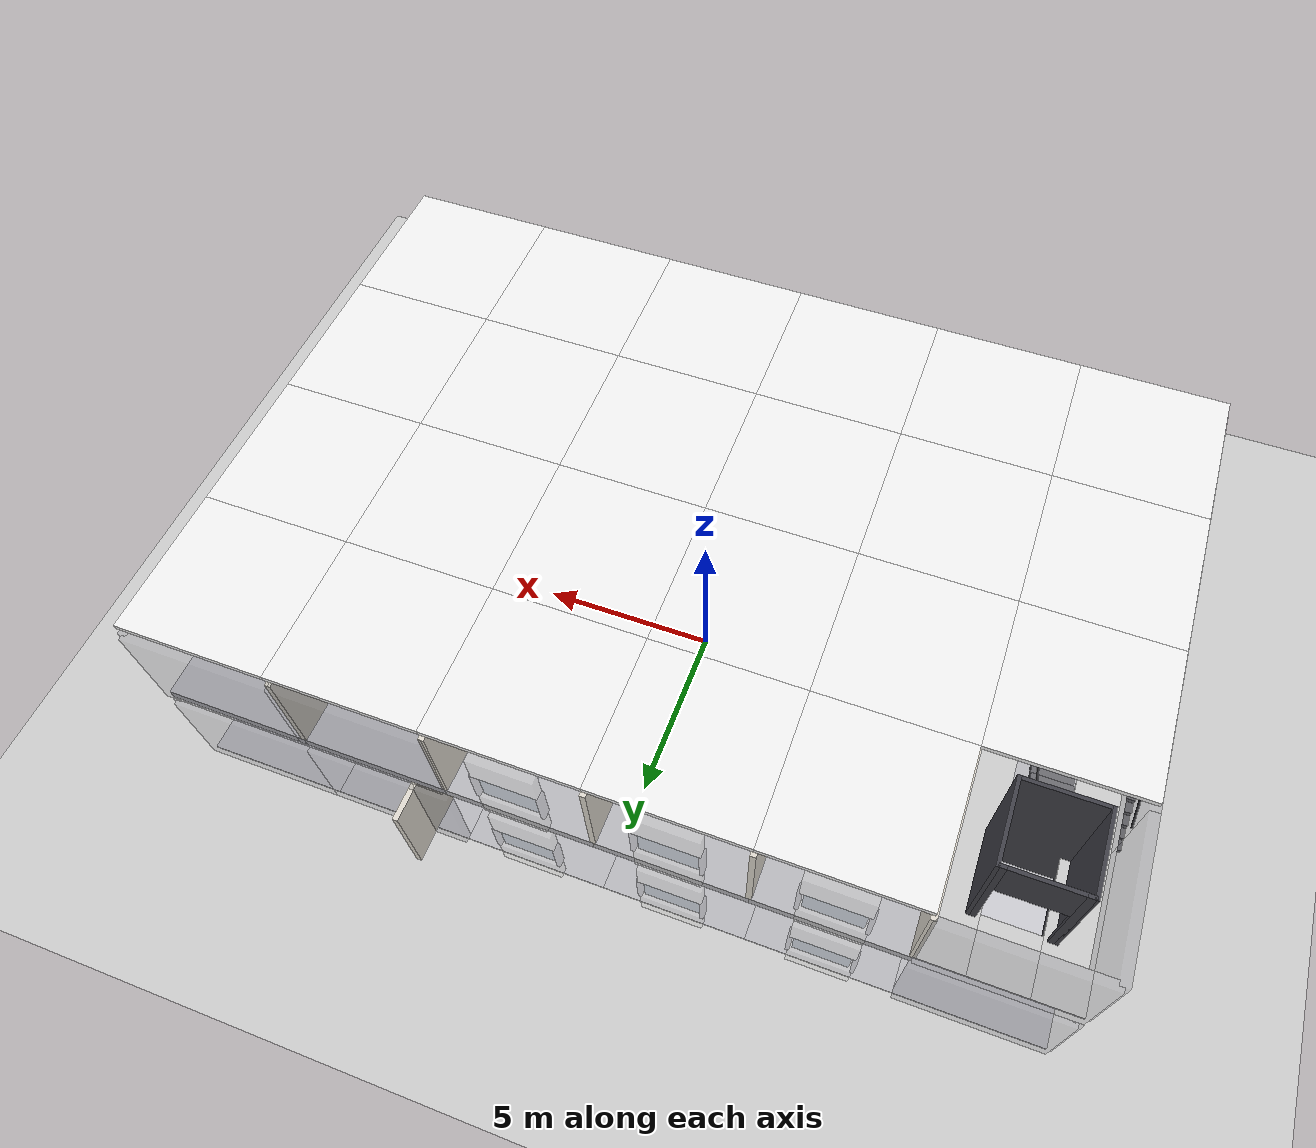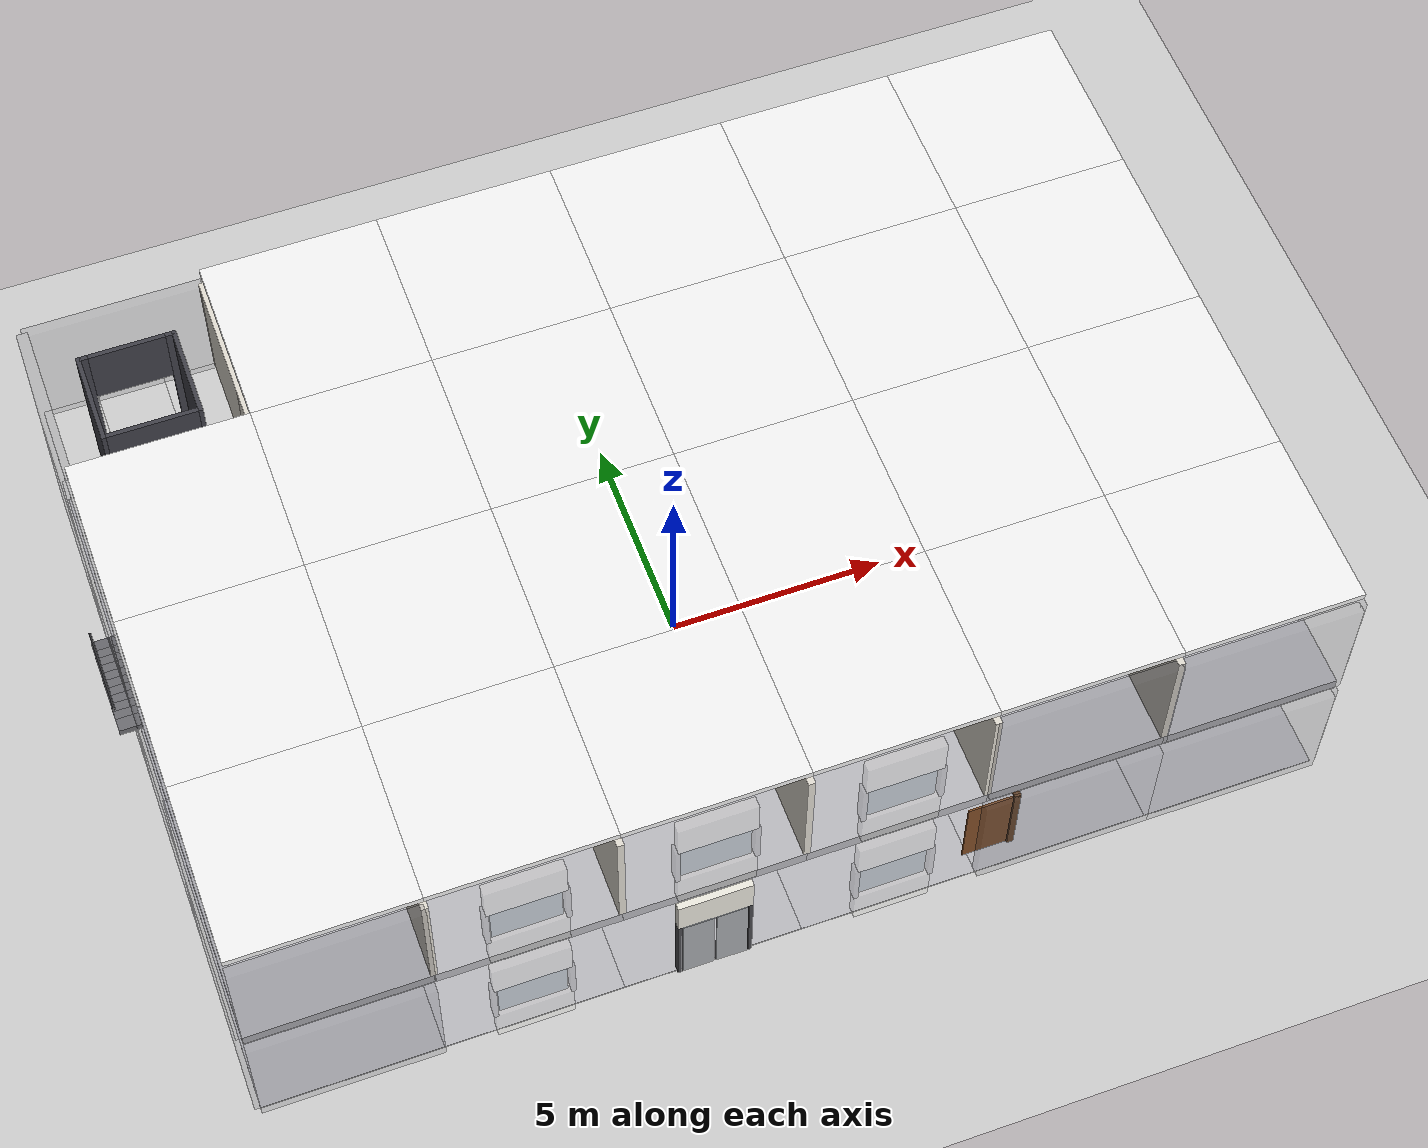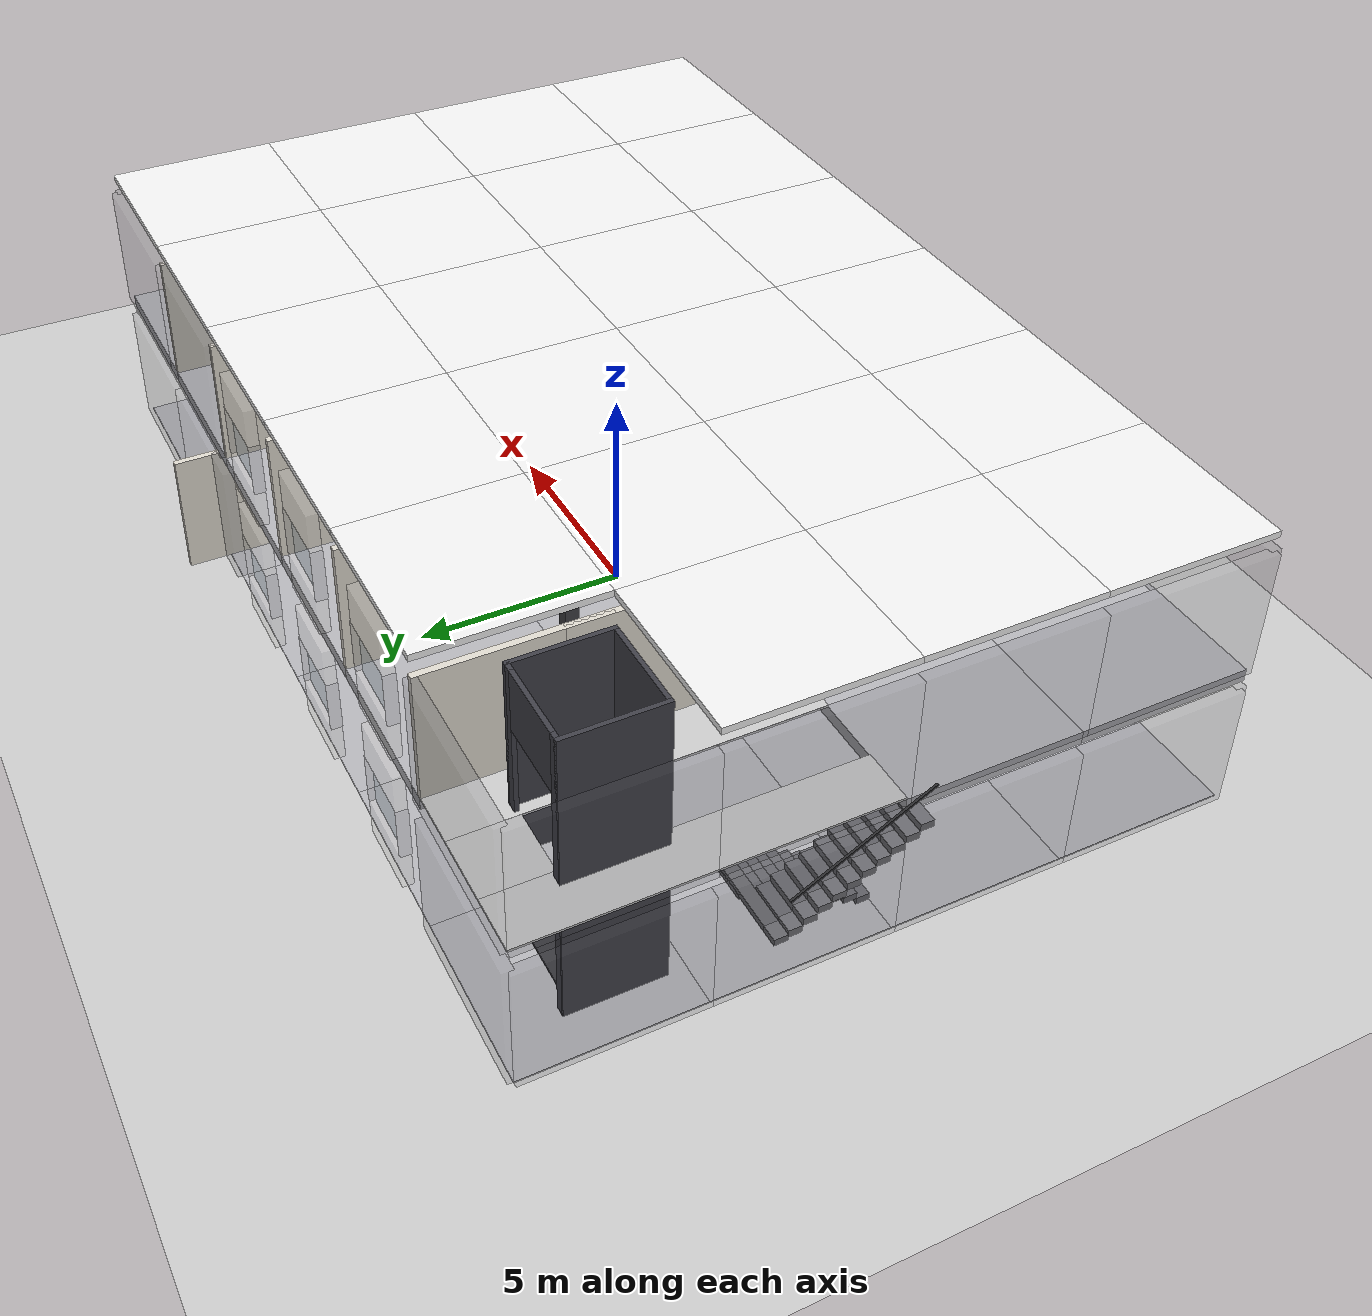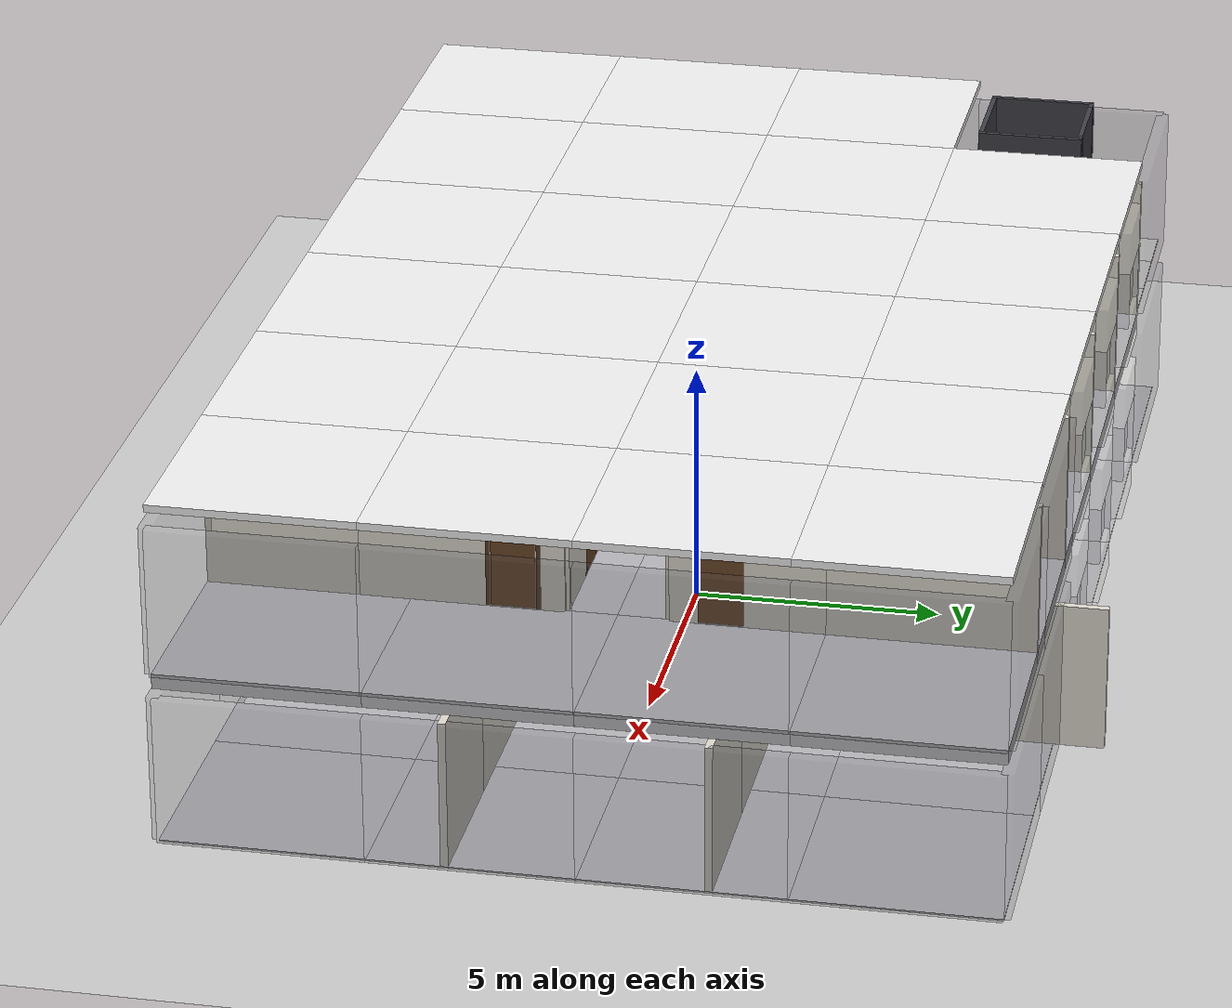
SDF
<?xml version="1.0" ?>
<sdf version="1.6">
  <world name="restaurant_empty_test">
    <!-- A global light source -->
    <include>
      <uri>model://sun</uri>
    </include>
    <!-- A ground plane -->
    <include>
      <uri>model://ground_plane</uri>
    </include>

    <physics type="ode">
      <max_step_size>0.001</max_step_size>
      <real_time_factor>1</real_time_factor>
      <real_time_update_rate>1000</real_time_update_rate>
    </physics>

    <!-- Ground Floor Structure Shell -->
    <!-- Floor Slabs (6x4 grid) -->
    <include><name>floor_slab_0_0</name><uri>model://_components/floor_slab</uri><pose>-10 -6 0 0 0 0</pose></include>
    <include><name>floor_slab_1_0</name><uri>model://_components/floor_slab</uri><pose>-6 -6 0 0 0 0</pose></include>
    <include><name>floor_slab_2_0</name><uri>model://_components/floor_slab</uri><pose>-2 -6 0 0 0 0</pose></include>
    <include><name>floor_slab_3_0</name><uri>model://_components/floor_slab</uri><pose>2 -6 0 0 0 0</pose></include>
    <include><name>floor_slab_4_0</name><uri>model://_components/floor_slab</uri><pose>6 -6 0 0 0 0</pose></include>
    <include><name>floor_slab_5_0</name><uri>model://_components/floor_slab</uri><pose>10 -6 0 0 0 0</pose></include>
    <include><name>floor_slab_0_1</name><uri>model://_components/floor_slab</uri><pose>-10 -2 0 0 0 0</pose></include>
    <include><name>floor_slab_1_1</name><uri>model://_components/floor_slab</uri><pose>-6 -2 0 0 0 0</pose></include>
    <include><name>floor_slab_2_1</name><uri>model://_components/floor_slab</uri><pose>-2 -2 0 0 0 0</pose></include>
    <include><name>floor_slab_3_1</name><uri>model://_components/floor_slab</uri><pose>2 -2 0 0 0 0</pose></include>
    <include><name>floor_slab_4_1</name><uri>model://_components/floor_slab</uri><pose>6 -2 0 0 0 0</pose></include>
    <include><name>floor_slab_5_1</name><uri>model://_components/floor_slab</uri><pose>10 -2 0 0 0 0</pose></include>
    <include><name>floor_slab_0_2</name><uri>model://_components/floor_slab</uri><pose>-10 2 0 0 0 0</pose></include>
    <include><name>floor_slab_1_2</name><uri>model://_components/floor_slab</uri><pose>-6 2 0 0 0 0</pose></include>
    <include><name>floor_slab_2_2</name><uri>model://_components/floor_slab</uri><pose>-2 2 0 0 0 0</pose></include>
    <include><name>floor_slab_3_2</name><uri>model://_components/floor_slab</uri><pose>2 2 0 0 0 0</pose></include>
    <include><name>floor_slab_4_2</name><uri>model://_components/floor_slab</uri><pose>6 2 0 0 0 0</pose></include>
    <include><name>floor_slab_5_2</name><uri>model://_components/floor_slab</uri><pose>10 2 0 0 0 0</pose></include>
    <include><name>floor_slab_0_3</name><uri>model://_components/floor_slab</uri><pose>-10 6 0 0 0 0</pose></include>
    <include><name>floor_slab_1_3</name><uri>model://_components/floor_slab</uri><pose>-6 6 0 0 0 0</pose></include>
    <include><name>floor_slab_2_3</name><uri>model://_components/floor_slab</uri><pose>-2 6 0 0 0 0</pose></include>
    <include><name>floor_slab_3_3</name><uri>model://_components/floor_slab</uri><pose>2 6 0 0 0 0</pose></include>
    <include><name>floor_slab_4_3</name><uri>model://_components/floor_slab</uri><pose>6 6 0 0 0 0</pose></include>
    <include><name>floor_slab_5_3</name><uri>model://_components/floor_slab</uri><pose>10 6 0 0 0 0</pose></include>

    <!-- Ground Floor Exterior Walls -->
    <include><name>ext_wall_s0</name><uri>model://_components/wall_exterior</uri><pose>-10 -8 0 0 0 0</pose></include>
    <include><name>ext_wall_s1</name><uri>model://_components/window_standard</uri><pose>-6 -8 0 0 0 0</pose></include>
    <include><name>ext_wall_s2</name><uri>model://_components/door_double</uri><pose>-2 -8 0 0 0 0</pose></include>
    <include><name>ext_wall_s3</name><uri>model://_components/window_standard</uri><pose>2 -8 0 0 0 0</pose></include>
    <include><name>ext_wall_s4</name><uri>model://_components/wall_exterior</uri><pose>6 -8 0 0 0 0</pose></include>
    <include><name>ext_wall_s5</name><uri>model://_components/wall_exterior</uri><pose>10 -8 0 0 0 0</pose></include>
    <include><name>ext_wall_n0</name><uri>model://_components/wall_exterior</uri><pose>-10 8 0 0 0 3.14159</pose></include>
    <include><name>ext_wall_n1</name><uri>model://_components/window_standard</uri><pose>-6 8 0 0 0 3.14159</pose></include>
    <include><name>ext_wall_n2</name><uri>model://_components/window_standard</uri><pose>-2 8 0 0 0 3.14159</pose></include>
    <include><name>ext_wall_n3</name><uri>model://_components/window_standard</uri><pose>2 8 0 0 0 3.14159</pose></include>
    <include><name>ext_wall_n4</name><uri>model://_components/wall_exterior</uri><pose>6 8 0 0 0 3.14159</pose></include>
    <include><name>ext_wall_n5</name><uri>model://_components/wall_exterior</uri><pose>10 8 0 0 0 3.14159</pose></include>
    <include><name>ext_wall_w0</name><uri>model://_components/wall_exterior</uri><pose>-12 -6 0 0 0 1.5708</pose></include>
    <include><name>ext_wall_w1</name><uri>model://_components/wall_exterior</uri><pose>-12 -2 0 0 0 1.5708</pose></include>
    <include><name>ext_wall_w2</name><uri>model://_components/wall_exterior</uri><pose>-12 2 0 0 0 1.5708</pose></include>
    <include><name>ext_wall_w3</name><uri>model://_components/wall_exterior</uri><pose>-12 6 0 0 0 1.5708</pose></include>
    <include><name>ext_wall_e0</name><uri>model://_components/wall_exterior</uri><pose>12 -6 0 0 0 1.5708</pose></include>
    <include><name>ext_wall_e1</name><uri>model://_components/wall_exterior</uri><pose>12 -2 0 0 0 1.5708</pose></include>
    <include><name>ext_wall_e2</name><uri>model://_components/wall_exterior</uri><pose>12 2 0 0 0 1.5708</pose></include>
    <include><name>ext_wall_e3</name><uri>model://_components/wall_exterior</uri><pose>12 6 0 0 0 1.5708</pose></include>

    <!-- Ground Floor Columns -->
    <include><name>column_0</name><uri>model://_components/column</uri><pose>-6 -4 0 0 0 0</pose></include>
    <include><name>column_1</name><uri>model://_components/column</uri><pose>-2 -4 0 0 0 0</pose></include>
    <include><name>column_2</name><uri>model://_components/column</uri><pose>2 -4 0 0 0 0</pose></include>
    <include><name>column_3</name><uri>model://_components/column</uri><pose>-6 4 0 0 0 0</pose></include>
    <include><name>column_4</name><uri>model://_components/column</uri><pose>-2 4 0 0 0 0</pose></include>
    <include><name>column_5</name><uri>model://_components/column</uri><pose>2 4 0 0 0 0</pose></include>

    <!-- Fixtures -->
    <include><name>stairs</name><uri>model://_fixtures/staircase</uri><pose>-10 0 0 0 0 1.5708</pose></include>
    <include><name>lift_shaft_inst</name><uri>model://_fixtures/lift_shaft</uri><pose>-10 5.5 0 0 0 0</pose></include>
    <include><name>lift_cabin_inst</name><uri>model://_fixtures/lift_cabin</uri><pose>-10 5.5 0 0 0 0</pose></include>

    <!-- Ground Floor Partition Walls -->
    <include><name>kitchen_partition_n</name><uri>model://_components/wall_segment_4m</uri><pose>5.0 7.0 0 0 0 1.5708</pose></include>
    <include><name>kitchen_partition_mid1</name><uri>model://_components/wall_segment</uri><pose>5.0 3.5 0 0 0 1.5708</pose></include>
    <include><name>kitchen_partition_mid2</name><uri>model://_components/wall_segment</uri><pose>5.0 1.5 0 0 0 1.5708</pose></include>
    <include><name>kitchen_partition_mid3</name><uri>model://_components/wall_segment</uri><pose>5.0 -1.5 0 0 0 1.5708</pose></include>
    <include><name>kitchen_partition_mid4</name><uri>model://_components/wall_segment</uri><pose>5.0 -3.5 0 0 0 1.5708</pose></include>
    <include><name>kitchen_wall_1_2_a</name><uri>model://_components/wall_segment_4m</uri><pose>7.0 2.5 0 0 0 0</pose></include>
    <include><name>kitchen_wall_1_2_b</name><uri>model://_components/wall_segment_4m</uri><pose>10.0 2.5 0 0 0 0</pose></include>
    <include><name>kitchen_wall_2_3_a</name><uri>model://_components/wall_segment_4m</uri><pose>7.0 -2.5 0 0 0 0</pose></include>
    <include><name>kitchen_wall_2_3_b</name><uri>model://_components/wall_segment_4m</uri><pose>10.0 -2.5 0 0 0 0</pose></include>
    <include><name>kitchen_door_1</name><uri>model://_components/door_single_wide</uri><pose>5.0 2.5 0 0 0 1.5708</pose></include>
    <include><name>kitchen_door_2</name><uri>model://_components/door_single_wide</uri><pose>5.0 -2.5 0 0 0 1.5708</pose></include>
    <include><name>kitchen_door_3</name><uri>model://_components/door_single_wide</uri><pose>5.0 -7.0 0 0 0 1.5708</pose></include>

    <!-- First Floor Structure Shell (placed at z = 3.5) -->
    <!-- Floor Slabs -->
    <include><name>f1_floor_slab_0_0</name><uri>model://_components/floor_slab</uri><pose>-10 -6 3.5 0 0 0</pose></include>
    <include><name>f1_floor_slab_1_0</name><uri>model://_components/floor_slab</uri><pose>-6 -6 3.5 0 0 0</pose></include>
    <include><name>f1_floor_slab_2_0</name><uri>model://_components/floor_slab</uri><pose>-2 -6 3.5 0 0 0</pose></include>
    <include><name>f1_floor_slab_3_0</name><uri>model://_components/floor_slab</uri><pose>2 -6 3.5 0 0 0</pose></include>
    <include><name>f1_floor_slab_4_0</name><uri>model://_components/floor_slab</uri><pose>6 -6 3.5 0 0 0</pose></include>
    <include><name>f1_floor_slab_5_0</name><uri>model://_components/floor_slab</uri><pose>10 -6 3.5 0 0 0</pose></include>
    <include><name>f1_floor_slab_0_1</name><uri>model://_components/floor_slab</uri><pose>-10 -2 3.5 0 0 0</pose></include>
    <include><name>f1_floor_slab_1_1</name><uri>model://_components/floor_slab</uri><pose>-6 -2 3.5 0 0 0</pose></include>
    <include><name>f1_floor_slab_2_1</name><uri>model://_components/floor_slab</uri><pose>-2 -2 3.5 0 0 0</pose></include>
    <include><name>f1_floor_slab_3_1</name><uri>model://_components/floor_slab</uri><pose>2 -2 3.5 0 0 0</pose></include>
    <include><name>f1_floor_slab_4_1</name><uri>model://_components/floor_slab</uri><pose>6 -2 3.5 0 0 0</pose></include>
    <include><name>f1_floor_slab_5_1</name><uri>model://_components/floor_slab</uri><pose>10 -2 3.5 0 0 0</pose></include>
    <include><name>f1_floor_slab_1_2</name><uri>model://_components/floor_slab</uri><pose>-6 2 3.5 0 0 0</pose></include>
    <include><name>f1_floor_slab_2_2</name><uri>model://_components/floor_slab</uri><pose>-2 2 3.5 0 0 0</pose></include>
    <include><name>f1_floor_slab_3_2</name><uri>model://_components/floor_slab</uri><pose>2 2 3.5 0 0 0</pose></include>
    <include><name>f1_floor_slab_4_2</name><uri>model://_components/floor_slab</uri><pose>6 2 3.5 0 0 0</pose></include>
    <include><name>f1_floor_slab_5_2</name><uri>model://_components/floor_slab</uri><pose>10 2 3.5 0 0 0</pose></include>
    <include><name>f1_floor_slab_1_3</name><uri>model://_components/floor_slab</uri><pose>-6 6 3.5 0 0 0</pose></include>
    <include><name>f1_floor_slab_2_3</name><uri>model://_components/floor_slab</uri><pose>-2 6 3.5 0 0 0</pose></include>
    <include><name>f1_floor_slab_3_3</name><uri>model://_components/floor_slab</uri><pose>2 6 3.5 0 0 0</pose></include>
    <include><name>f1_floor_slab_4_3</name><uri>model://_components/floor_slab</uri><pose>6 6 3.5 0 0 0</pose></include>
    <include><name>f1_floor_slab_5_3</name><uri>model://_components/floor_slab</uri><pose>10 6 3.5 0 0 0</pose></include>

    <!-- First Floor Walking area fillers -->
    <model name="f1_fillers">
      <static>true</static>
      <link name="link">
        <pose>0 0 0 0 0 0</pose>
        <collision name="strip_l">
          <pose>-11.375 4.0 3.525 0 0 0</pose>
          <geometry><box><size>1.25 8.0 0.05</size></box></geometry>
        </collision>
        <visual name="strip_l">
          <pose>-11.375 4.0 3.525 0 0 0</pose>
          <geometry><box><size>1.25 8.0 0.05</size></box></geometry>
          <material><ambient>0.8 0.8 0.8 1</ambient><diffuse>0.8 0.8 0.8 1</diffuse></material>
        </visual>
        <collision name="strip_r">
          <pose>-8.625 4.0 3.525 0 0 0</pose>
          <geometry><box><size>1.25 8.0 0.05</size></box></geometry>
        </collision>
        <visual name="strip_r">
          <pose>-8.625 4.0 3.525 0 0 0</pose>
          <geometry><box><size>1.25 8.0 0.05</size></box></geometry>
          <material><ambient>0.8 0.8 0.8 1</ambient><diffuse>0.8 0.8 0.8 1</diffuse></material>
        </visual>
        <collision name="strip_n">
          <pose>-10.0 7.25 3.525 0 0 0</pose>
          <geometry><box><size>1.5 1.5 0.05</size></box></geometry>
        </collision>
        <visual name="strip_n">
          <pose>-10.0 7.25 3.525 0 0 0</pose>
          <geometry><box><size>1.5 1.5 0.05</size></box></geometry>
          <material><ambient>0.8 0.8 0.8 1</ambient><diffuse>0.8 0.8 0.8 1</diffuse></material>
        </visual>
      </link>
    </model>

    <!-- First Floor Exterior Walls -->
    <include><name>f1_ext_wall_s0</name><uri>model://_components/wall_exterior</uri><pose>-10 -8 3.5 0 0 0</pose></include>
    <include><name>f1_ext_wall_s1</name><uri>model://_components/window_standard</uri><pose>-6 -8 3.5 0 0 0</pose></include>
    <include><name>f1_ext_wall_s2</name><uri>model://_components/window_standard</uri><pose>-2 -8 3.5 0 0 0</pose></include>
    <include><name>f1_ext_wall_s3</name><uri>model://_components/window_standard</uri><pose>2 -8 3.5 0 0 0</pose></include>
    <include><name>f1_ext_wall_s4</name><uri>model://_components/wall_exterior</uri><pose>6 -8 3.5 0 0 0</pose></include>
    <include><name>f1_ext_wall_s5</name><uri>model://_components/wall_exterior</uri><pose>10 -8 3.5 0 0 0</pose></include>
    <include><name>f1_ext_wall_n0</name><uri>model://_components/wall_exterior</uri><pose>-10 8 3.5 0 0 3.14159</pose></include>
    <include><name>f1_ext_wall_n1</name><uri>model://_components/window_standard</uri><pose>-6 8 3.5 0 0 3.14159</pose></include>
    <include><name>f1_ext_wall_n2</name><uri>model://_components/window_standard</uri><pose>-2 8 3.5 0 0 3.14159</pose></include>
    <include><name>f1_ext_wall_n3</name><uri>model://_components/window_standard</uri><pose>2 8 3.5 0 0 3.14159</pose></include>
    <include><name>f1_ext_wall_n4</name><uri>model://_components/wall_exterior</uri><pose>6 8 3.5 0 0 3.14159</pose></include>
    <include><name>f1_ext_wall_n5</name><uri>model://_components/wall_exterior</uri><pose>10 8 3.5 0 0 3.14159</pose></include>
    <include><name>f1_ext_wall_w0</name><uri>model://_components/wall_exterior</uri><pose>-12 -6 3.5 0 0 1.5708</pose></include>
    <include><name>f1_ext_wall_w1</name><uri>model://_components/wall_exterior</uri><pose>-12 -2 3.5 0 0 1.5708</pose></include>
    <include><name>f1_ext_wall_w2</name><uri>model://_components/wall_exterior</uri><pose>-12 2 3.5 0 0 1.5708</pose></include>
    <include><name>f1_ext_wall_w3</name><uri>model://_components/wall_exterior</uri><pose>-12 6 3.5 0 0 1.5708</pose></include>
    <include><name>f1_ext_wall_e0</name><uri>model://_components/wall_exterior</uri><pose>12 -6 3.5 0 0 1.5708</pose></include>
    <include><name>f1_ext_wall_e1</name><uri>model://_components/wall_exterior</uri><pose>12 -2 3.5 0 0 1.5708</pose></include>
    <include><name>f1_ext_wall_e2</name><uri>model://_components/wall_exterior</uri><pose>12 2 3.5 0 0 1.5708</pose></include>
    <include><name>f1_ext_wall_e3</name><uri>model://_components/wall_exterior</uri><pose>12 6 3.5 0 0 1.5708</pose></include>

    <!-- First Floor Columns -->
    <include><name>f1_column_0</name><uri>model://_components/column</uri><pose>-6 -4 3.5 0 0 0</pose></include>
    <include><name>f1_column_1</name><uri>model://_components/column</uri><pose>-2 -4 3.5 0 0 0</pose></include>
    <include><name>f1_column_2</name><uri>model://_components/column</uri><pose>2 -4 3.5 0 0 0</pose></include>
    <include><name>f1_column_3</name><uri>model://_components/column</uri><pose>-6 4 3.5 0 0 0</pose></include>
    <include><name>f1_column_4</name><uri>model://_components/column</uri><pose>-2 4 3.5 0 0 0</pose></include>
    <include><name>f1_column_5</name><uri>model://_components/column</uri><pose>2 4 3.5 0 0 0</pose></include>

    <!-- First Floor Corridor Partition Walls -->
    <include><name>f1_corridor_n_wall_1</name><uri>model://_components/wall_segment_4m</uri><pose>-6 1.0 3.5 0 0 0</pose></include>
    <include><name>f1_corridor_n_wall_2</name><uri>model://_components/wall_segment_4m</uri><pose>-2 1.0 3.5 0 0 0</pose></include>
    <include><name>f1_corridor_n_wall_3</name><uri>model://_components/wall_segment_4m</uri><pose>2 1.0 3.5 0 0 0</pose></include>
    <include><name>f1_corridor_n_wall_4</name><uri>model://_components/wall_segment_4m</uri><pose>6 1.0 3.5 0 0 0</pose></include>
    <include><name>f1_corridor_s_wall_1</name><uri>model://_components/wall_segment_4m</uri><pose>-6 -1.0 3.5 0 0 0</pose></include>
    <include><name>f1_corridor_s_wall_2</name><uri>model://_components/wall_segment_4m</uri><pose>-2 -1.0 3.5 0 0 0</pose></include>
    <include><name>f1_corridor_s_wall_3</name><uri>model://_components/wall_segment_4m</uri><pose>2 -1.0 3.5 0 0 0</pose></include>
    <include><name>f1_corridor_s_wall_4</name><uri>model://_components/wall_segment_4m</uri><pose>6 -1.0 3.5 0 0 0</pose></include>
    <include><name>f1_cabin_door_1</name><uri>model://_components/door_single</uri><pose>-6 1.0 3.5 0 0 0</pose></include>
    <include><name>f1_cabin_door_2</name><uri>model://_components/door_single</uri><pose>-2 1.0 3.5 0 0 0</pose></include>
    <include><name>f1_cabin_door_3</name><uri>model://_components/door_single</uri><pose>2 1.0 3.5 0 0 0</pose></include>
    <include><name>f1_cabin_door_4</name><uri>model://_components/door_single</uri><pose>6 1.0 3.5 0 0 0</pose></include>
    <include><name>f1_cabin_door_5</name><uri>model://_components/door_single</uri><pose>-6 -1.0 3.5 0 0 3.14159</pose></include>
    <include><name>f1_cabin_door_6</name><uri>model://_components/door_single</uri><pose>-2 -1.0 3.5 0 0 3.14159</pose></include>
    <include><name>f1_cabin_door_7</name><uri>model://_components/door_single</uri><pose>2 -1.0 3.5 0 0 3.14159</pose></include>
    <include><name>f1_cabin_door_8</name><uri>model://_components/door_single</uri><pose>6 -1.0 3.5 0 0 3.14159</pose></include>

    <!-- First Floor Cabin Division Walls -->
    <include><name>f1_div_wall_n0_a</name><uri>model://_components/wall_segment_4m</uri><pose>-8 3.0 3.5 0 0 1.5708</pose></include>
    <include><name>f1_div_wall_n0_b</name><uri>model://_components/wall_segment_4m</uri><pose>-8 6.0 3.5 0 0 1.5708</pose></include>
    <include><name>f1_div_wall_n1_a</name><uri>model://_components/wall_segment_4m</uri><pose>-4 3.0 3.5 0 0 1.5708</pose></include>
    <include><name>f1_div_wall_n1_b</name><uri>model://_components/wall_segment_4m</uri><pose>-4 6.0 3.5 0 0 1.5708</pose></include>
    <include><name>f1_div_wall_n2_a</name><uri>model://_components/wall_segment_4m</uri><pose>0 3.0 3.5 0 0 1.5708</pose></include>
    <include><name>f1_div_wall_n2_b</name><uri>model://_components/wall_segment_4m</uri><pose>0 6.0 3.5 0 0 1.5708</pose></include>
    <include><name>f1_div_wall_n3_a</name><uri>model://_components/wall_segment_4m</uri><pose>4 3.0 3.5 0 0 1.5708</pose></include>
    <include><name>f1_div_wall_n3_b</name><uri>model://_components/wall_segment_4m</uri><pose>4 6.0 3.5 0 0 1.5708</pose></include>
    <include><name>f1_div_wall_n4_a</name><uri>model://_components/wall_segment_4m</uri><pose>8 3.0 3.5 0 0 1.5708</pose></include>
    <include><name>f1_div_wall_n4_b</name><uri>model://_components/wall_segment_4m</uri><pose>8 6.0 3.5 0 0 1.5708</pose></include>
    <include><name>f1_div_wall_s0_a</name><uri>model://_components/wall_segment_4m</uri><pose>-8 -3.0 3.5 0 0 1.5708</pose></include>
    <include><name>f1_div_wall_s0_b</name><uri>model://_components/wall_segment_4m</uri><pose>-8 -6.0 3.5 0 0 1.5708</pose></include>
    <include><name>f1_div_wall_s1_a</name><uri>model://_components/wall_segment_4m</uri><pose>-4 -3.0 3.5 0 0 1.5708</pose></include>
    <include><name>f1_div_wall_s1_b</name><uri>model://_components/wall_segment_4m</uri><pose>-4 -6.0 3.5 0 0 1.5708</pose></include>
    <include><name>f1_div_wall_s2_a</name><uri>model://_components/wall_segment_4m</uri><pose>0 -3.0 3.5 0 0 1.5708</pose></include>
    <include><name>f1_div_wall_s2_b</name><uri>model://_components/wall_segment_4m</uri><pose>0 -6.0 3.5 0 0 1.5708</pose></include>
    <include><name>f1_div_wall_s3_a</name><uri>model://_components/wall_segment_4m</uri><pose>4 -3.0 3.5 0 0 1.5708</pose></include>
    <include><name>f1_div_wall_s3_b</name><uri>model://_components/wall_segment_4m</uri><pose>4 -6.0 3.5 0 0 1.5708</pose></include>
    <include><name>f1_div_wall_s4_a</name><uri>model://_components/wall_segment_4m</uri><pose>8 -3.0 3.5 0 0 1.5708</pose></include>
    <include><name>f1_div_wall_s4_b</name><uri>model://_components/wall_segment_4m</uri><pose>8 -6.0 3.5 0 0 1.5708</pose></include>
    <include><name>f1_utility_door_n</name><uri>model://_components/door_single</uri><pose>8 2.0 3.5 0 0 1.5708</pose></include>
    <include><name>f1_utility_door_s</name><uri>model://_components/door_single</uri><pose>8 -2.0 3.5 0 0 1.5708</pose></include>

    <!-- First Floor Ceiling Slabs (Roof) -->
    <include><name>f1_ceil_slab_0_0</name><uri>model://_components/ceiling_slab</uri><pose>-10 -6 6.9 0 0 0</pose></include>
    <include><name>f1_ceil_slab_1_0</name><uri>model://_components/ceiling_slab</uri><pose>-6 -6 6.9 0 0 0</pose></include>
    <include><name>f1_ceil_slab_2_0</name><uri>model://_components/ceiling_slab</uri><pose>-2 -6 6.9 0 0 0</pose></include>
    <include><name>f1_ceil_slab_3_0</name><uri>model://_components/ceiling_slab</uri><pose>2 -6 6.9 0 0 0</pose></include>
    <include><name>f1_ceil_slab_4_0</name><uri>model://_components/ceiling_slab</uri><pose>6 -6 6.9 0 0 0</pose></include>
    <include><name>f1_ceil_slab_5_0</name><uri>model://_components/ceiling_slab</uri><pose>10 -6 6.9 0 0 0</pose></include>
    <include><name>f1_ceil_slab_0_1</name><uri>model://_components/ceiling_slab</uri><pose>-10 -2 6.9 0 0 0</pose></include>
    <include><name>f1_ceil_slab_1_1</name><uri>model://_components/ceiling_slab</uri><pose>-6 -2 6.9 0 0 0</pose></include>
    <include><name>f1_ceil_slab_2_1</name><uri>model://_components/ceiling_slab</uri><pose>-2 -2 6.9 0 0 0</pose></include>
    <include><name>f1_ceil_slab_3_1</name><uri>model://_components/ceiling_slab</uri><pose>2 -2 6.9 0 0 0</pose></include>
    <include><name>f1_ceil_slab_4_1</name><uri>model://_components/ceiling_slab</uri><pose>6 -2 6.9 0 0 0</pose></include>
    <include><name>f1_ceil_slab_5_1</name><uri>model://_components/ceiling_slab</uri><pose>10 -2 6.9 0 0 0</pose></include>
    <include><name>f1_ceil_slab_0_2</name><uri>model://_components/ceiling_slab</uri><pose>-10 2 6.9 0 0 0</pose></include>
    <include><name>f1_ceil_slab_1_2</name><uri>model://_components/ceiling_slab</uri><pose>-6 2 6.9 0 0 0</pose></include>
    <include><name>f1_ceil_slab_2_2</name><uri>model://_components/ceiling_slab</uri><pose>-2 2 6.9 0 0 0</pose></include>
    <include><name>f1_ceil_slab_3_2</name><uri>model://_components/ceiling_slab</uri><pose>2 2 6.9 0 0 0</pose></include>
    <include><name>f1_ceil_slab_4_2</name><uri>model://_components/ceiling_slab</uri><pose>6 2 6.9 0 0 0</pose></include>
    <include><name>f1_ceil_slab_5_2</name><uri>model://_components/ceiling_slab</uri><pose>10 2 6.9 0 0 0</pose></include>
    <include><name>f1_ceil_slab_1_3</name><uri>model://_components/ceiling_slab</uri><pose>-6 6 6.9 0 0 0</pose></include>
    <include><name>f1_ceil_slab_2_3</name><uri>model://_components/ceiling_slab</uri><pose>-2 6 6.9 0 0 0</pose></include>
    <include><name>f1_ceil_slab_3_3</name><uri>model://_components/ceiling_slab</uri><pose>2 6 6.9 0 0 0</pose></include>
    <include><name>f1_ceil_slab_4_3</name><uri>model://_components/ceiling_slab</uri><pose>6 6 6.9 0 0 0</pose></include>
    <include><name>f1_ceil_slab_5_3</name><uri>model://_components/ceiling_slab</uri><pose>10 6 6.9 0 0 0</pose></include>

  </world>
</sdf>

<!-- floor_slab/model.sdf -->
<sdf version="1.6">
  <model name="floor_slab">
    <static>true</static>
    <link name="floor_link">
      <pose>0 0 -0.15 0 0 0</pose>
      <collision name="floor_col">
        <geometry><box><size>4.0 4.0 0.30</size></box></geometry>
        <surface>
          <friction><ode><mu>0.9</mu><mu2>0.9</mu2></ode></friction>
        </surface>
      </collision>
      <visual name="floor_vis">
        <geometry><box><size>4.0 4.0 0.30</size></box></geometry>
        <material>
          <!-- Polished porcelain: light grey, strong specular sheen -->
          <ambient>0.55 0.55 0.57 1</ambient>
          <diffuse>0.72 0.72 0.74 1</diffuse>
          <specular>0.55 0.55 0.57 1</specular>
          <emissive>0 0 0 1</emissive>
        </material>
      </visual>
    </link>
  </model>
</sdf>

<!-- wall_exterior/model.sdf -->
<sdf version="1.6">
  <model name="wall_exterior">
    <static>true</static>
    <link name="link">
      <pose>0 0 1.5 0 0 0</pose>
      <collision name="collision">
        <geometry>
          <box>
            <size>4.0 0.25 3.0</size>
          </box>
        </geometry>
      </collision>
      <visual name="visual">
        <geometry>
          <box>
            <size>4.0 0.25 3.0</size>
          </box>
        </geometry>
        <material>
          <ambient>0.35 0.35 0.38 1</ambient>
          <diffuse>0.35 0.35 0.38 1</diffuse>
          <specular>0.2 0.2 0.2 1</specular>
        </material>
        <transparency>0.85</transparency>
      </visual>
    </link>
  </model>
</sdf>

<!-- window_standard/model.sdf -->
<sdf version="1.6">
  <model name="window_standard">
    <static>true</static>
    <link name="frame_link">
      <!-- Sill (below glass) fill: z 0.0 -> 0.9 -->
      <collision name="sill_col">
        <pose>0 0 0.45 0 0 0</pose>
        <geometry><box><size>1.7 0.25 0.9</size></box></geometry>
      </collision>
      <visual name="sill_vis">
        <pose>0 0 0.45 0 0 0</pose>
        <geometry><box><size>1.7 0.25 0.9</size></box></geometry>
        <material><ambient>0.85 0.84 0.80 1</ambient><diffuse>0.92 0.91 0.87 1</diffuse><specular>0.05 0.05 0.05 1</specular></material>
        <transparency>0.85</transparency>
      </visual>

      <!-- Header (above glass): z 2.1 -> 3.0 -->
      <collision name="header_col">
        <pose>0 0 2.55 0 0 0</pose>
        <geometry><box><size>1.7 0.25 0.9</size></box></geometry>
      </collision>
      <visual name="header_vis">
        <pose>0 0 2.55 0 0 0</pose>
        <geometry><box><size>1.7 0.25 0.9</size></box></geometry>
        <material><ambient>0.85 0.84 0.80 1</ambient><diffuse>0.92 0.91 0.87 1</diffuse><specular>0.05 0.05 0.05 1</specular></material>
        <transparency>0.85</transparency>
      </visual>

      <!-- Left mullion -->
      <collision name="mull_left_col">
        <pose>-0.85 0 1.5 0 0 0</pose>
        <geometry><box><size>0.10 0.25 1.2</size></box></geometry>
      </collision>
      <visual name="mull_left_vis">
        <pose>-0.85 0 1.5 0 0 0</pose>
        <geometry><box><size>0.10 0.25 1.2</size></box></geometry>
        <material><ambient>0.30 0.30 0.32 1</ambient><diffuse>0.38 0.38 0.40 1</diffuse><specular>0.25 0.25 0.27 1</specular></material>
        <transparency>0.85</transparency>
      </visual>
      <!-- Right mullion -->
      <collision name="mull_right_col">
        <pose>0.85 0 1.5 0 0 0</pose>
        <geometry><box><size>0.10 0.25 1.2</size></box></geometry>
      </collision>
      <visual name="mull_right_vis">
        <pose>0.85 0 1.5 0 0 0</pose>
        <geometry><box><size>0.10 0.25 1.2</size></box></geometry>
        <material><ambient>0.30 0.30 0.32 1</ambient><diffuse>0.38 0.38 0.40 1</diffuse><specular>0.25 0.25 0.27 1</specular></material>
        <transparency>0.85</transparency>
      </visual>
    </link>

    <!-- ===== GLASS (visual only) ===== -->
    <link name="glass_link">
      <pose>0 0 1.5 0 0 0</pose>
      <visual name="glass_vis">
        <geometry><box><size>1.5 0.03 1.2</size></box></geometry>
        <material>
          <!-- Cool tinted transparent glass -->
          <ambient>0.35 0.45 0.50 0.30</ambient>
          <diffuse>0.45 0.55 0.60 0.30</diffuse>
          <specular>0.70 0.70 0.72 0.30</specular>
        </material>
        <transparency>0.7</transparency>
      </visual>
    </link>
  </model>
</sdf>

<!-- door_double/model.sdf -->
<sdf version="1.6">
  <model name="door_double">
    <static>true</static>
    <link name="frame_link">
      <collision name="jamb_left_col">
        <pose>-0.79 0 1.05 0 0 0</pose>
        <geometry><box><size>0.08 0.15 2.1</size></box></geometry>
      </collision>
      <visual name="jamb_left_vis">
        <pose>-0.79 0 1.05 0 0 0</pose>
        <geometry><box><size>0.08 0.15 2.1</size></box></geometry>
        <material><ambient>0.20 0.20 0.22 1</ambient><diffuse>0.28 0.28 0.30 1</diffuse><specular>0.30 0.30 0.32 1</specular></material>
      </visual>
      <collision name="jamb_right_col">
        <pose>0.79 0 1.05 0 0 0</pose>
        <geometry><box><size>0.08 0.15 2.1</size></box></geometry>
      </collision>
      <visual name="jamb_right_vis">
        <pose>0.79 0 1.05 0 0 0</pose>
        <geometry><box><size>0.08 0.15 2.1</size></box></geometry>
        <material><ambient>0.20 0.20 0.22 1</ambient><diffuse>0.28 0.28 0.30 1</diffuse><specular>0.30 0.30 0.32 1</specular></material>
      </visual>
      <collision name="head_col">
        <pose>0 0 2.55 0 0 0</pose>
        <geometry><box><size>1.66 0.15 0.9</size></box></geometry>
      </collision>
      <visual name="head_vis">
        <pose>0 0 2.55 0 0 0</pose>
        <geometry><box><size>1.66 0.15 0.9</size></box></geometry>
        <material><ambient>0.85 0.84 0.80 1</ambient><diffuse>0.92 0.91 0.87 1</diffuse><specular>0.05 0.05 0.05 1</specular></material>
      </visual>
    </link>

    <link name="leaf_left">
      <pose>-0.375 -0.06 1.05 0 0 0</pose>
      <collision name="col"><geometry><box><size>0.70 0.04 2.05</size></box></geometry></collision>
      <visual name="vis">
        <geometry><box><size>0.70 0.04 2.05</size></box></geometry>
        <!-- Brushed-metal look via high specular -->
        <material><ambient>0.55 0.56 0.58 1</ambient><diffuse>0.65 0.66 0.68 1</diffuse><specular>0.60 0.60 0.62 1</specular></material>
      </visual>
    </link>
    <link name="leaf_right">
      <pose>0.375 -0.06 1.05 0 0 0</pose>
      <collision name="col"><geometry><box><size>0.70 0.04 2.05</size></box></geometry></collision>
      <visual name="vis">
        <geometry><box><size>0.70 0.04 2.05</size></box></geometry>
        <material><ambient>0.55 0.56 0.58 1</ambient><diffuse>0.65 0.66 0.68 1</diffuse><specular>0.60 0.60 0.62 1</specular></material>
      </visual>
    </link>
  </model>
</sdf>

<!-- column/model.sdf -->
<!--
  column | Module A - Structural Components
  0.30 x 0.30 m footprint, 3.0 m tall. Bottom at z=0. Origin at footprint centre, floor level.
-->
<sdf version="1.6">
  <model name="column">
    <static>true</static>
    <link name="column_link">
      <pose>0 0 1.5 0 0 0</pose>
      <collision name="column_col">
        <geometry><box><size>0.30 0.30 3.0</size></box></geometry>
      </collision>
      <visual name="column_vis">
        <geometry><box><size>0.30 0.30 3.0</size></box></geometry>
        <material>
          <!-- Premium charcoal cladding -->
          <ambient>0.18 0.18 0.20 1</ambient>
          <diffuse>0.25 0.25 0.27 1</diffuse>
          <specular>0.30 0.30 0.32 1</specular>
        </material>
      </visual>
    </link>
  </model>
</sdf>

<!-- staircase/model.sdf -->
<sdf version="1.6">
  <model name="staircase">
    <static>true</static>

    <!-- ===================== FLIGHT A (steps 1..10, +X, Y 0..1.2) ===================== -->
    <link name="flight_a">
      <!-- Step template repeated; tread 0.30, rise 0.165, top of step n at n*0.165 -->
      <!-- Step 1 -->
      <collision name="a1_col"><pose>0.15 0.6 0.0825 0 0 0</pose><geometry><box><size>0.30 1.2 0.165</size></box></geometry></collision>
      <visual name="a1_vis"><pose>0.15 0.6 0.0825 0 0 0</pose><geometry><box><size>0.30 1.2 0.165</size></box></geometry>
        <material><ambient>0.30 0.30 0.32 1</ambient><diffuse>0.42 0.42 0.44 1</diffuse><specular>0.30 0.30 0.32 1</specular></material></visual>
      <!-- Step 2 -->
      <collision name="a2_col"><pose>0.45 0.6 0.2475 0 0 0</pose><geometry><box><size>0.30 1.2 0.165</size></box></geometry></collision>
      <visual name="a2_vis"><pose>0.45 0.6 0.2475 0 0 0</pose><geometry><box><size>0.30 1.2 0.165</size></box></geometry>
        <material><ambient>0.30 0.30 0.32 1</ambient><diffuse>0.42 0.42 0.44 1</diffuse><specular>0.30 0.30 0.32 1</specular></material></visual>
      <!-- Step 3 -->
      <collision name="a3_col"><pose>0.75 0.6 0.4125 0 0 0</pose><geometry><box><size>0.30 1.2 0.165</size></box></geometry></collision>
      <visual name="a3_vis"><pose>0.75 0.6 0.4125 0 0 0</pose><geometry><box><size>0.30 1.2 0.165</size></box></geometry>
        <material><ambient>0.30 0.30 0.32 1</ambient><diffuse>0.42 0.42 0.44 1</diffuse><specular>0.30 0.30 0.32 1</specular></material></visual>
      <!-- Step 4 -->
      <collision name="a4_col"><pose>1.05 0.6 0.5775 0 0 0</pose><geometry><box><size>0.30 1.2 0.165</size></box></geometry></collision>
      <visual name="a4_vis"><pose>1.05 0.6 0.5775 0 0 0</pose><geometry><box><size>0.30 1.2 0.165</size></box></geometry>
        <material><ambient>0.30 0.30 0.32 1</ambient><diffuse>0.42 0.42 0.44 1</diffuse><specular>0.30 0.30 0.32 1</specular></material></visual>
      <!-- Step 5 -->
      <collision name="a5_col"><pose>1.35 0.6 0.7425 0 0 0</pose><geometry><box><size>0.30 1.2 0.165</size></box></geometry></collision>
      <visual name="a5_vis"><pose>1.35 0.6 0.7425 0 0 0</pose><geometry><box><size>0.30 1.2 0.165</size></box></geometry>
        <material><ambient>0.30 0.30 0.32 1</ambient><diffuse>0.42 0.42 0.44 1</diffuse><specular>0.30 0.30 0.32 1</specular></material></visual>
      <!-- Step 6 -->
      <collision name="a6_col"><pose>1.65 0.6 0.9075 0 0 0</pose><geometry><box><size>0.30 1.2 0.165</size></box></geometry></collision>
      <visual name="a6_vis"><pose>1.65 0.6 0.9075 0 0 0</pose><geometry><box><size>0.30 1.2 0.165</size></box></geometry>
        <material><ambient>0.30 0.30 0.32 1</ambient><diffuse>0.42 0.42 0.44 1</diffuse><specular>0.30 0.30 0.32 1</specular></material></visual>
      <!-- Step 7 -->
      <collision name="a7_col"><pose>1.95 0.6 1.0725 0 0 0</pose><geometry><box><size>0.30 1.2 0.165</size></box></geometry></collision>
      <visual name="a7_vis"><pose>1.95 0.6 1.0725 0 0 0</pose><geometry><box><size>0.30 1.2 0.165</size></box></geometry>
        <material><ambient>0.30 0.30 0.32 1</ambient><diffuse>0.42 0.42 0.44 1</diffuse><specular>0.30 0.30 0.32 1</specular></material></visual>
      <!-- Step 8 -->
      <collision name="a8_col"><pose>2.25 0.6 1.2375 0 0 0</pose><geometry><box><size>0.30 1.2 0.165</size></box></geometry></collision>
      <visual name="a8_vis"><pose>2.25 0.6 1.2375 0 0 0</pose><geometry><box><size>0.30 1.2 0.165</size></box></geometry>
        <material><ambient>0.30 0.30 0.32 1</ambient><diffuse>0.42 0.42 0.44 1</diffuse><specular>0.30 0.30 0.32 1</specular></material></visual>
      <!-- Step 9 -->
      <collision name="a9_col"><pose>2.55 0.6 1.4025 0 0 0</pose><geometry><box><size>0.30 1.2 0.165</size></box></geometry></collision>
      <visual name="a9_vis"><pose>2.55 0.6 1.4025 0 0 0</pose><geometry><box><size>0.30 1.2 0.165</size></box></geometry>
        <material><ambient>0.30 0.30 0.32 1</ambient><diffuse>0.42 0.42 0.44 1</diffuse><specular>0.30 0.30 0.32 1</specular></material></visual>
      <!-- Step 10 -->
      <collision name="a10_col"><pose>2.85 0.6 1.5675 0 0 0</pose><geometry><box><size>0.30 1.2 0.165</size></box></geometry></collision>
      <visual name="a10_vis"><pose>2.85 0.6 1.5675 0 0 0</pose><geometry><box><size>0.30 1.2 0.165</size></box></geometry>
        <material><ambient>0.30 0.30 0.32 1</ambient><diffuse>0.42 0.42 0.44 1</diffuse><specular>0.30 0.30 0.32 1</specular></material></visual>
    </link>

    <!-- ===================== LANDING (at z=1.65, X 2.7..3.0, Y 0..2.5) ===================== -->
    <link name="landing">
      <collision name="landing_col"><pose>2.85 1.25 1.6425 0 0 0</pose><geometry><box><size>0.30 2.5 0.15</size></box></geometry></collision>
      <visual name="landing_vis"><pose>2.85 1.25 1.6425 0 0 0</pose><geometry><box><size>0.30 2.5 0.15</size></box></geometry>
        <material><ambient>0.28 0.28 0.30 1</ambient><diffuse>0.40 0.40 0.42 1</diffuse><specular>0.35 0.35 0.37 1</specular></material></visual>
    </link>

    <!-- ===================== FLIGHT B (steps 11..20, -X, Y 1.3..2.5) ===================== -->
    <link name="flight_b">
      <!-- Step 11 (first above landing 1.65) -->
      <collision name="b11_col"><pose>2.55 1.9 1.7325 0 0 0</pose><geometry><box><size>0.30 1.2 0.165</size></box></geometry></collision>
      <visual name="b11_vis"><pose>2.55 1.9 1.7325 0 0 0</pose><geometry><box><size>0.30 1.2 0.165</size></box></geometry>
        <material><ambient>0.30 0.30 0.32 1</ambient><diffuse>0.42 0.42 0.44 1</diffuse><specular>0.30 0.30 0.32 1</specular></material></visual>
      <collision name="b12_col"><pose>2.25 1.9 1.8975 0 0 0</pose><geometry><box><size>0.30 1.2 0.165</size></box></geometry></collision>
      <visual name="b12_vis"><pose>2.25 1.9 1.8975 0 0 0</pose><geometry><box><size>0.30 1.2 0.165</size></box></geometry>
        <material><ambient>0.30 0.30 0.32 1</ambient><diffuse>0.42 0.42 0.44 1</diffuse><specular>0.30 0.30 0.32 1</specular></material></visual>
      <collision name="b13_col"><pose>1.95 1.9 2.0625 0 0 0</pose><geometry><box><size>0.30 1.2 0.165</size></box></geometry></collision>
      <visual name="b13_vis"><pose>1.95 1.9 2.0625 0 0 0</pose><geometry><box><size>0.30 1.2 0.165</size></box></geometry>
        <material><ambient>0.30 0.30 0.32 1</ambient><diffuse>0.42 0.42 0.44 1</diffuse><specular>0.30 0.30 0.32 1</specular></material></visual>
      <collision name="b14_col"><pose>1.65 1.9 2.2275 0 0 0</pose><geometry><box><size>0.30 1.2 0.165</size></box></geometry></collision>
      <visual name="b14_vis"><pose>1.65 1.9 2.2275 0 0 0</pose><geometry><box><size>0.30 1.2 0.165</size></box></geometry>
        <material><ambient>0.30 0.30 0.32 1</ambient><diffuse>0.42 0.42 0.44 1</diffuse><specular>0.30 0.30 0.32 1</specular></material></visual>
      <collision name="b15_col"><pose>1.35 1.9 2.3925 0 0 0</pose><geometry><box><size>0.30 1.2 0.165</size></box></geometry></collision>
      <visual name="b15_vis"><pose>1.35 1.9 2.3925 0 0 0</pose><geometry><box><size>0.30 1.2 0.165</size></box></geometry>
        <material><ambient>0.30 0.30 0.32 1</ambient><diffuse>0.42 0.42 0.44 1</diffuse><specular>0.30 0.30 0.32 1</specular></material></visual>
      <collision name="b16_col"><pose>1.05 1.9 2.5575 0 0 0</pose><geometry><box><size>0.30 1.2 0.165</size></box></geometry></collision>
      <visual name="b16_vis"><pose>1.05 1.9 2.5575 0 0 0</pose><geometry><box><size>0.30 1.2 0.165</size></box></geometry>
        <material><ambient>0.30 0.30 0.32 1</ambient><diffuse>0.42 0.42 0.44 1</diffuse><specular>0.30 0.30 0.32 1</specular></material></visual>
      <collision name="b17_col"><pose>0.75 1.9 2.7225 0 0 0</pose><geometry><box><size>0.30 1.2 0.165</size></box></geometry></collision>
      <visual name="b17_vis"><pose>0.75 1.9 2.7225 0 0 0</pose><geometry><box><size>0.30 1.2 0.165</size></box></geometry>
        <material><ambient>0.30 0.30 0.32 1</ambient><diffuse>0.42 0.42 0.44 1</diffuse><specular>0.30 0.30 0.32 1</specular></material></visual>
      <collision name="b18_col"><pose>0.45 1.9 2.8875 0 0 0</pose><geometry><box><size>0.30 1.2 0.165</size></box></geometry></collision>
      <visual name="b18_vis"><pose>0.45 1.9 2.8875 0 0 0</pose><geometry><box><size>0.30 1.2 0.165</size></box></geometry>
        <material><ambient>0.30 0.30 0.32 1</ambient><diffuse>0.42 0.42 0.44 1</diffuse><specular>0.30 0.30 0.32 1</specular></material></visual>
      <collision name="b19_col"><pose>0.15 1.9 3.0525 0 0 0</pose><geometry><box><size>0.30 1.2 0.165</size></box></geometry></collision>
      <visual name="b19_vis"><pose>0.15 1.9 3.0525 0 0 0</pose><geometry><box><size>0.30 1.2 0.165</size></box></geometry>
        <material><ambient>0.30 0.30 0.32 1</ambient><diffuse>0.42 0.42 0.44 1</diffuse><specular>0.30 0.30 0.32 1</specular></material></visual>
      <!-- 20 (top, reaches 3.30) -->
      <collision name="b20_col"><pose>-0.15 1.9 3.2175 0 0 0</pose><geometry><box><size>0.30 1.2 0.165</size></box></geometry></collision>
      <visual name="b20_vis"><pose>-0.15 1.9 3.2175 0 0 0</pose><geometry><box><size>0.30 1.2 0.165</size></box></geometry>
        <material><ambient>0.30 0.30 0.32 1</ambient><diffuse>0.42 0.42 0.44 1</diffuse><specular>0.30 0.30 0.32 1</specular></material></visual>
    </link>

    <!-- ===================== HANDRAIL (visual only, both flights outer edge) ===================== -->
    <link name="handrail">
      <!-- Flight A outer rail (Y=0.02), rising: walking line runs (0,0)->(3.0,1.65),
           rail offset +0.9m vertically above the pitch line, centered on the run -->
      <visual name="rail_a_vis"><pose>1.5 0.03 1.725 0 -0.5 0</pose>
        <geometry><box><size>3.4 0.05 0.05</size></box></geometry>
        <material><ambient>0.10 0.10 0.11 1</ambient><diffuse>0.16 0.16 0.17 1</diffuse><specular>0.40 0.40 0.42 1</specular></material></visual>
      <!-- Flight B outer rail (Y=2.48), rising the other way: walking line runs
           (2.7,1.65)->(-0.3,3.30), rail offset +0.9m vertically above the pitch line -->
      <visual name="rail_b_vis"><pose>1.2 2.47 3.375 0 0.5 0</pose>
        <geometry><box><size>3.4 0.05 0.05</size></box></geometry>
        <material><ambient>0.10 0.10 0.11 1</ambient><diffuse>0.16 0.16 0.17 1</diffuse><specular>0.40 0.40 0.42 1</specular></material></visual>
    </link>
  </model>
</sdf>

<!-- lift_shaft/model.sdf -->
<sdf version="1.6">
  <model name="lift_shaft">
    <static>true</static>
    <link name="link">
      <pose>0 0 0 0 0 0</pose>
      <!-- Left Wall (Solid) -->
      <collision name="left_wall_collision">
        <pose>-1.05 0 3.5 0 0 0</pose>
        <geometry><box><size>0.1 2.2 7.0</size></box></geometry>
      </collision>
      <visual name="left_wall_visual">
        <pose>-1.05 0 3.5 0 0 0</pose>
        <geometry><box><size>0.1 2.2 7.0</size></box></geometry>
        <material>
          <ambient>0.25 0.25 0.28 1</ambient>
          <diffuse>0.25 0.25 0.28 1</diffuse>
          <specular>0.4 0.4 0.4 1</specular>
        </material>
      </visual>

      <!-- Right Wall (Solid) -->
      <collision name="right_wall_collision">
        <pose>1.05 0 3.5 0 0 0</pose>
        <geometry><box><size>0.1 2.2 7.0</size></box></geometry>
      </collision>
      <visual name="right_wall_visual">
        <pose>1.05 0 3.5 0 0 0</pose>
        <geometry><box><size>0.1 2.2 7.0</size></box></geometry>
        <material>
          <ambient>0.25 0.25 0.28 1</ambient>
          <diffuse>0.25 0.25 0.28 1</diffuse>
          <specular>0.4 0.4 0.4 1</specular>
        </material>
      </visual>

      <!-- Back Wall (Solid) -->
      <collision name="back_wall_collision">
        <pose>0 -1.05 3.5 0 0 0</pose>
        <geometry><box><size>2.0 0.1 7.0</size></box></geometry>
      </collision>
      <visual name="back_wall_visual">
        <pose>0 -1.05 3.5 0 0 0</pose>
        <geometry><box><size>2.0 0.1 7.0</size></box></geometry>
        <material>
          <ambient>0.25 0.25 0.28 1</ambient>
          <diffuse>0.25 0.25 0.28 1</diffuse>
          <specular>0.4 0.4 0.4 1</specular>
        </material>
      </visual>

      <!-- Front Wall (with door openings) -->
      <!-- Left corner post -->
      <collision name="front_left_post_collision">
        <pose>-0.95 1.05 3.5 0 0 0</pose>
        <geometry><box><size>0.2 0.1 7.0</size></box></geometry>
      </collision>
      <visual name="front_left_post_visual">
        <pose>-0.95 1.05 3.5 0 0 0</pose>
        <geometry><box><size>0.2 0.1 7.0</size></box></geometry>
        <material>
          <ambient>0.25 0.25 0.28 1</ambient>
          <diffuse>0.25 0.25 0.28 1</diffuse>
        </material>
      </visual>

      <!-- Right corner post -->
      <collision name="front_right_post_collision">
        <pose>0.95 1.05 3.5 0 0 0</pose>
        <geometry><box><size>0.2 0.1 7.0</size></box></geometry>
      </collision>
      <visual name="front_right_post_visual">
        <pose>0.95 1.05 3.5 0 0 0</pose>
        <geometry><box><size>0.2 0.1 7.0</size></box></geometry>
        <material>
          <ambient>0.25 0.25 0.28 1</ambient>
          <diffuse>0.25 0.25 0.28 1</diffuse>
        </material>
      </visual>

      <!-- Middle beam (separating ground floor and first floor openings) -->
      <collision name="front_mid_beam_collision">
        <pose>0 1.05 2.8 0 0 0</pose>
        <geometry><box><size>1.7 0.1 1.4</size></box></geometry>
      </collision>
      <visual name="front_mid_beam_visual">
        <pose>0 1.05 2.8 0 0 0</pose>
        <geometry><box><size>1.7 0.1 1.4</size></box></geometry>
        <material>
          <ambient>0.25 0.25 0.28 1</ambient>
          <diffuse>0.25 0.25 0.28 1</diffuse>
        </material>
      </visual>

      <!-- Top beam (above first floor opening) -->
      <collision name="front_top_beam_collision">
        <pose>0 1.05 6.3 0 0 0</pose>
        <geometry><box><size>1.7 0.1 1.4</size></box></geometry>
      </collision>
      <visual name="front_top_beam_visual">
        <pose>0 1.05 6.3 0 0 0</pose>
        <geometry><box><size>1.7 0.1 1.4</size></box></geometry>
        <material>
          <ambient>0.25 0.25 0.28 1</ambient>
          <diffuse>0.25 0.25 0.28 1</diffuse>
        </material>
      </visual>
    </link>
  </model>
</sdf>

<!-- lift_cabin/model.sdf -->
<sdf version="1.6">
  <model name="lift_cabin">
    <static>true</static>
    <link name="link">
      <pose>0 0 0 0 0 0</pose>
      <!-- Floor Slab -->
      <collision name="floor_collision">
        <pose>0 0 0.025 0 0 0</pose>
        <geometry><box><size>1.8 1.8 0.05</size></box></geometry>
      </collision>
      <visual name="floor_visual">
        <pose>0 0 0.025 0 0 0</pose>
        <geometry><box><size>1.8 1.8 0.05</size></box></geometry>
        <material>
          <ambient>0.2 0.2 0.22 1</ambient>
          <diffuse>0.2 0.2 0.22 1</diffuse>
        </material>
      </visual>
      <!-- Left Wall -->
      <collision name="left_wall_collision">
        <pose>-0.875 0 1.2 0 0 0</pose>
        <geometry><box><size>0.05 1.8 2.3</size></box></geometry>
      </collision>
      <visual name="left_wall_visual">
        <pose>-0.875 0 1.2 0 0 0</pose>
        <geometry><box><size>0.05 1.8 2.3</size></box></geometry>
        <material>
          <ambient>0.7 0.7 0.72 1</ambient>
          <diffuse>0.7 0.7 0.72 1</diffuse>
          <specular>0.7 0.7 0.72 1</specular>
        </material>
      </visual>
      <!-- Right Wall -->
      <collision name="right_wall_collision">
        <pose>0.875 0 1.2 0 0 0</pose>
        <geometry><box><size>0.05 1.8 2.3</size></box></geometry>
      </collision>
      <visual name="right_wall_visual">
        <pose>0.875 0 1.2 0 0 0</pose>
        <geometry><box><size>0.05 1.8 2.3</size></box></geometry>
        <material>
          <ambient>0.7 0.7 0.72 1</ambient>
          <diffuse>0.7 0.7 0.72 1</diffuse>
          <specular>0.7 0.7 0.72 1</specular>
        </material>
      </visual>
      <!-- Back Wall -->
      <collision name="back_wall_collision">
        <pose>0 -0.875 1.2 0 0 0</pose>
        <geometry><box><size>1.8 0.05 2.3</size></box></geometry>
      </collision>
      <visual name="back_wall_visual">
        <pose>0 -0.875 1.2 0 0 0</pose>
        <geometry><box><size>1.8 0.05 2.3</size></box></geometry>
        <material>
          <ambient>0.7 0.7 0.72 1</ambient>
          <diffuse>0.7 0.7 0.72 1</diffuse>
          <specular>0.7 0.7 0.72 1</specular>
        </material>
      </visual>
      <!-- Roof -->
      <collision name="roof_collision">
        <pose>0 0 2.375 0 0 0</pose>
        <geometry><box><size>1.8 1.8 0.05</size></box></geometry>
      </collision>
      <visual name="roof_visual">
        <pose>0 0 2.375 0 0 0</pose>
        <geometry><box><size>1.8 1.8 0.05</size></box></geometry>
        <material>
          <ambient>0.8 0.8 0.82 1</ambient>
          <diffuse>0.8 0.8 0.82 1</diffuse>
        </material>
      </visual>
      <!-- Small interior ceiling panel light -->
      <visual name="light_panel">
        <pose>0 0 2.34 0 0 0</pose>
        <geometry><box><size>0.5 0.5 0.02</size></box></geometry>
        <material>
          <ambient>1.0 1.0 1.0 1</ambient>
          <diffuse>1.0 1.0 1.0 1</diffuse>
          <emissive>1.0 1.0 1.0 1</emissive>
        </material>
      </visual>
    </link>
  </model>
</sdf>

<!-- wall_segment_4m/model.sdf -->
<sdf version="1.6">
  <model name="wall_segment_4m">
    <static>true</static>
    <link name="link">
      <pose>0 0 1.5 0 0 0</pose>
      <collision name="collision">
        <geometry>
          <box>
            <size>4.0 0.15 3.0</size>
          </box>
        </geometry>
      </collision>
      <visual name="visual">
        <geometry>
          <box>
            <size>4.0 0.15 3.0</size>
          </box>
        </geometry>
        <material>
          <ambient>0.88 0.86 0.82 1</ambient>
          <diffuse>0.88 0.86 0.82 1</diffuse>
          <specular>0.1 0.1 0.1 1</specular>
        </material>
      </visual>
    </link>
  </model>
</sdf>

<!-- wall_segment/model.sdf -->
<sdf version="1.6">
  <model name="wall_segment">
    <static>true</static>

    <link name="wall_link">
      <!-- Lift the box so its bottom sits on the floor (half of 3.0 m). -->
      <pose>0 0 1.5 0 0 0</pose>

      <collision name="wall_collision">
        <geometry>
          <box>
            <size>1.0 0.15 3.0</size>
          </box>
        </geometry>
        <surface>
          <contact>
            <ode>
              <kp>1e7</kp>
              <kd>1.0</kd>
            </ode>
          </contact>
          <friction>
            <ode>
              <mu>0.8</mu>
              <mu2>0.8</mu2>
            </ode>
          </friction>
        </surface>
      </collision>

      <visual name="wall_visual">
        <geometry>
          <box>
            <size>1.0 0.15 3.0</size>
          </box>
        </geometry>
        <material>
          <!-- Premium warm off-white matte plaster -->
          <ambient>0.85 0.84 0.80 1</ambient>
          <diffuse>0.92 0.91 0.87 1</diffuse>
          <specular>0.05 0.05 0.05 1</specular>
          <emissive>0 0 0 1</emissive>
        </material>
      </visual>
    </link>
  </model>
</sdf>

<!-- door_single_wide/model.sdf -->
<sdf version="1.6">
  <model name="door_single_wide">
    <static>true</static>
    <link name="frame">
      <pose>0 0 0 0 0 0</pose>
      <!-- Left Post -->
      <collision name="left_post_collision">
        <pose>-0.575 0 1.05 0 0 0</pose>
        <geometry><box><size>0.05 0.15 2.1</size></box></geometry>
      </collision>
      <visual name="left_post_visual">
        <pose>-0.575 0 1.05 0 0 0</pose>
        <geometry><box><size>0.05 0.15 2.1</size></box></geometry>
        <material>
          <ambient>0.4 0.25 0.13 1</ambient>
          <diffuse>0.4 0.25 0.13 1</diffuse>
        </material>
      </visual>
      <!-- Right Post -->
      <collision name="right_post_collision">
        <pose>0.575 0 1.05 0 0 0</pose>
        <geometry><box><size>0.05 0.15 2.1</size></box></geometry>
      </collision>
      <visual name="right_post_visual">
        <pose>0.575 0 1.05 0 0 0</pose>
        <geometry><box><size>0.05 0.15 2.1</size></box></geometry>
        <material>
          <ambient>0.4 0.25 0.13 1</ambient>
          <diffuse>0.4 0.25 0.13 1</diffuse>
        </material>
      </visual>
      <!-- Header -->
      <collision name="header_collision">
        <pose>0 0 2.075 0 0 0</pose>
        <geometry><box><size>1.2 0.15 0.05</size></box></geometry>
      </collision>
      <visual name="header_visual">
        <pose>0 0 2.075 0 0 0</pose>
        <geometry><box><size>1.2 0.15 0.05</size></box></geometry>
        <material>
          <ambient>0.4 0.25 0.13 1</ambient>
          <diffuse>0.4 0.25 0.13 1</diffuse>
        </material>
      </visual>
      <!-- Open Door Panel (rotated 90 deg, extending along +y) -->
      <collision name="panel_collision">
        <pose>-0.53 0.55 1.0 0 0 1.5708</pose>
        <geometry><box><size>1.1 0.04 2.0</size></box></geometry>
      </collision>
      <visual name="panel_visual">
        <pose>-0.53 0.55 1.0 0 0 1.5708</pose>
        <geometry><box><size>1.1 0.04 2.0</size></box></geometry>
        <material>
          <ambient>0.5 0.3 0.15 1</ambient>
          <diffuse>0.5 0.3 0.15 1</diffuse>
        </material>
      </visual>
    </link>
  </model>
</sdf>

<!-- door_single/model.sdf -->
<sdf version="1.6">
  <model name="door_single">
    <static>true</static>

    <!-- ===== FRAME ===== -->
    <link name="frame_link">
      <!-- Left jamb -->
      <collision name="jamb_left_col">
        <pose>-0.49 0 1.05 0 0 0</pose>
        <geometry><box><size>0.08 0.15 2.1</size></box></geometry>
      </collision>
      <visual name="jamb_left_vis">
        <pose>-0.49 0 1.05 0 0 0</pose>
        <geometry><box><size>0.08 0.15 2.1</size></box></geometry>
        <material>
          <ambient>0.28 0.18 0.10 1</ambient>
          <diffuse>0.35 0.22 0.12 1</diffuse>
          <specular>0.10 0.08 0.05 1</specular>
        </material>
      </visual>

      <!-- Right jamb -->
      <collision name="jamb_right_col">
        <pose>0.49 0 1.05 0 0 0</pose>
        <geometry><box><size>0.08 0.15 2.1</size></box></geometry>
      </collision>
      <visual name="jamb_right_vis">
        <pose>0.49 0 1.05 0 0 0</pose>
        <geometry><box><size>0.08 0.15 2.1</size></box></geometry>
        <material>
          <ambient>0.28 0.18 0.10 1</ambient>
          <diffuse>0.35 0.22 0.12 1</diffuse>
          <specular>0.10 0.08 0.05 1</specular>
        </material>
      </visual>

      <!-- Head / lintel (spans 0.9 clear + jambs, from z=2.1 up to 3.0 fill) -->
      <collision name="head_col">
        <pose>0 0 2.55 0 0 0</pose>
        <geometry><box><size>1.06 0.15 0.9</size></box></geometry>
      </collision>
      <visual name="head_vis">
        <pose>0 0 2.55 0 0 0</pose>
        <geometry><box><size>1.06 0.15 0.9</size></box></geometry>
        <material>
          <ambient>0.85 0.84 0.80 1</ambient>
          <diffuse>0.92 0.91 0.87 1</diffuse>
          <specular>0.05 0.05 0.05 1</specular>
        </material>
      </visual>
    </link>

    <!-- ===== LEAF (held open flat, no path obstruction) ===== -->
    <link name="leaf_link">
      <!-- Placed flush inside the reveal, offset in Y so it doesn't block the 0.9 m opening -->
      <pose>0 -0.06 1.05 0 0 0</pose>
      <collision name="leaf_col">
        <!-- Thin leaf; kept out of the walkway plane -->
        <geometry><box><size>0.86 0.04 2.05</size></box></geometry>
      </collision>
      <visual name="leaf_vis">
        <geometry><box><size>0.86 0.04 2.05</size></box></geometry>
        <material>
          <ambient>0.32 0.20 0.11 1</ambient>
          <diffuse>0.42 0.27 0.15 1</diffuse>
          <specular>0.15 0.12 0.08 1</specular>
        </material>
      </visual>
    </link>

  </model>
</sdf>

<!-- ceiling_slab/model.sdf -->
<sdf version="1.6">
  <model name="ceiling_slab">
    <static>true</static>
    <link name="ceiling_link">
      <collision name="ceiling_col">
        <geometry><box><size>4.0 4.0 0.15</size></box></geometry>
      </collision>
      <visual name="ceiling_vis">
        <geometry><box><size>4.0 4.0 0.15</size></box></geometry>
        <material>
          <!-- Clean premium white ceiling, slight sheen -->
          <ambient>0.90 0.90 0.90 1</ambient>
          <diffuse>0.95 0.95 0.95 1</diffuse>
          <specular>0.08 0.08 0.08 1</specular>
        </material>
      </visual>
    </link>
  </model>
</sdf>
